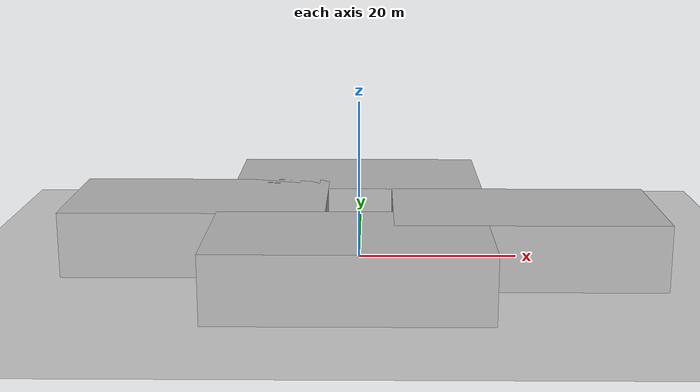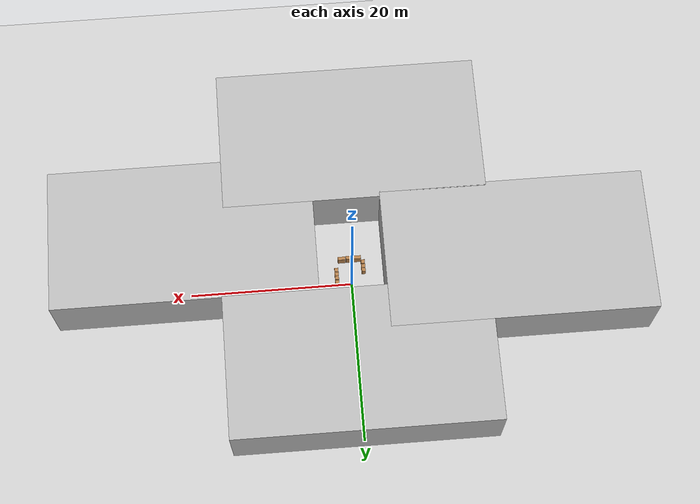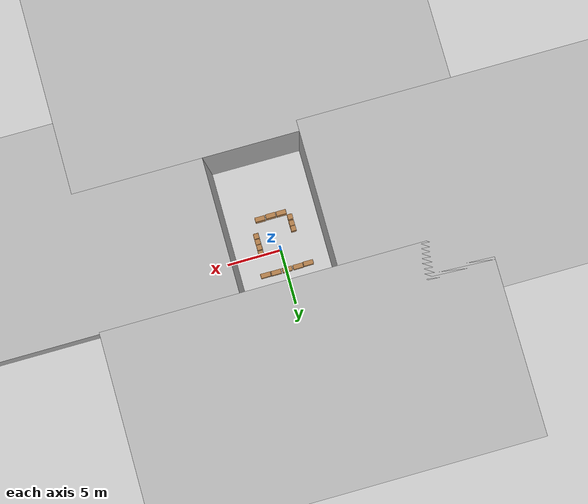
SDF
<sdf version='1.7'>
  <world name='default'>
  <plugin filename="gz-sim-physics-system" name="gz::sim::systems::Physics"></plugin>
  <plugin filename="gz-sim-user-commands-system" name="gz::sim::systems::UserCommands"></plugin>
  <plugin filename="gz-sim-scene-broadcaster-system" name="gz::sim::systems::SceneBroadcaster"></plugin>
  <plugin filename="gz-sim-sensors-system" name="gz::sim::systems::Sensors">
    <render_engine>ogre2</render_engine>
  </plugin>
    <light name='sun' type='directional'>
      <cast_shadows>1</cast_shadows>
      <pose>0 0 10 0 -0 0</pose>
      <diffuse>0.8 0.8 0.8 1</diffuse>
      <specular>0.2 0.2 0.2 1</specular>
      <attenuation>
        <range>1000</range>
        <constant>0.9</constant>
        <linear>0.01</linear>
        <quadratic>0.001</quadratic>
      </attenuation>
      <direction>-0.5 0.1 -0.9</direction>
      <spot>
        <inner_angle>0</inner_angle>
        <outer_angle>0</outer_angle>
        <falloff>0</falloff>
      </spot>
    </light>
    <model name='ground_plane'>
      <static>1</static>
      <link name='link'>
        <collision name='collision'>
          <geometry>
            <plane>
              <normal>0 0 1</normal>
              <size>100 100</size>
            </plane>
          </geometry>
          <surface>
            <contact>
              <collide_bitmask>65535</collide_bitmask>
              <ode/>
            </contact>
            <friction>
              <ode>
                <mu>100</mu>
                <mu2>50</mu2>
              </ode>
              <torsional>
                <ode/>
              </torsional>
            </friction>
            <bounce/>
          </surface>
          <max_contacts>10</max_contacts>
        </collision>
        <visual name='visual'>
          <cast_shadows>0</cast_shadows>
          <geometry>
            <plane>
              <normal>0 0 1</normal>
              <size>100 100</size>
            </plane>
          </geometry>
          <material>
            <script>
              <uri>file://media/materials/scripts/gazebo.material</uri>
              <name>Gazebo/Grey</name>
            </script>
          </material>
        </visual>
        <self_collide>0</self_collide>
        <enable_wind>0</enable_wind>
        <kinematic>0</kinematic>
      </link>
    </model>
    <gravity>0 0 -9.8</gravity>
    <magnetic_field>6e-06 2.3e-05 -4.2e-05</magnetic_field>
    <atmosphere type='adiabatic'/>
    <physics type='ode'>
      <max_step_size>0.001</max_step_size>
      <real_time_factor>1</real_time_factor>
      <real_time_update_rate>1000</real_time_update_rate>
    </physics>
    <scene>
      <ambient>0.4 0.4 0.4 1</ambient>
      <background>0.7 0.7 0.7 1</background>
      <shadows>1</shadows>
    </scene>
    <audio>
      <device>default</device>
    </audio>
    <wind/>
    <spherical_coordinates>
      <surface_model>EARTH_WGS84</surface_model>
      <latitude_deg>0</latitude_deg>
      <longitude_deg>0</longitude_deg>
      <elevation>0</elevation>
      <heading_deg>0</heading_deg>
    </spherical_coordinates>
    <model name='cabinet'>
      <static>1</static>
      <link name='cabinet_bottom_plate'>
        <inertial>
          <pose>0 0 -1 0 -0 0</pose>
          <inertia>
            <ixx>2.05</ixx>
            <ixy>0</ixy>
            <ixz>0</ixz>
            <iyy>2.05</iyy>
            <iyz>0</iyz>
            <izz>2.05</izz>
          </inertia>
          <mass>25</mass>
        </inertial>
        <collision name='cabinet_bottom_plate_geom'>
          <pose>0 0 0.01 0 -0 0</pose>
          <geometry>
            <box>
              <size>0.45 0.45 0.02</size>
            </box>
          </geometry>
          <max_contacts>10</max_contacts>
          <surface>
            <contact>
              <ode/>
            </contact>
            <bounce/>
            <friction>
              <torsional>
                <ode/>
              </torsional>
              <ode/>
            </friction>
          </surface>
        </collision>
        <visual name='cabinet_bottom_plate_geom_visual'>
          <pose>0 0 0.01 0 -0 0</pose>
          <geometry>
            <box>
              <size>0.45 0.45 0.02</size>
            </box>
          </geometry>
          <material>
            <script>
              <uri>file://media/materials/scripts/gazebo.material</uri>
              <name>Gazebo/Wood</name>
            </script>
          </material>
        </visual>
        <collision name='cabinet_bottom_plate_geom_cabinet_back_plate'>
          <pose>0.235 0 0.51 0 -0 0</pose>
          <geometry>
            <box>
              <size>0.02 0.45 1.02</size>
            </box>
          </geometry>
          <max_contacts>10</max_contacts>
          <surface>
            <contact>
              <ode/>
            </contact>
            <bounce/>
            <friction>
              <torsional>
                <ode/>
              </torsional>
              <ode/>
            </friction>
          </surface>
        </collision>
        <visual name='cabinet_bottom_plate_geom_cabinet_back_plate_visual'>
          <pose>0.235 0 0.51 0 -0 0</pose>
          <geometry>
            <box>
              <size>0.02 0.45 1.02</size>
            </box>
          </geometry>
          <material>
            <script>
              <uri>file://media/materials/scripts/gazebo.material</uri>
              <name>Gazebo/Wood</name>
            </script>
          </material>
        </visual>
        <collision name='cabinet_bottom_plate_geom_cabinet_left_plate'>
          <pose>0 0.235 0.51 0 -0 0</pose>
          <geometry>
            <box>
              <size>0.45 0.02 1.02</size>
            </box>
          </geometry>
          <max_contacts>10</max_contacts>
          <surface>
            <contact>
              <ode/>
            </contact>
            <bounce/>
            <friction>
              <torsional>
                <ode/>
              </torsional>
              <ode/>
            </friction>
          </surface>
        </collision>
        <visual name='cabinet_bottom_plate_geom_cabinet_left_plate_visual'>
          <pose>0 0.235 0.51 0 -0 0</pose>
          <geometry>
            <box>
              <size>0.45 0.02 1.02</size>
            </box>
          </geometry>
          <material>
            <script>
              <uri>file://media/materials/scripts/gazebo.material</uri>
              <name>Gazebo/Wood</name>
            </script>
          </material>
        </visual>
        <collision name='cabinet_bottom_plate_geom_cabinet_middle_plate'>
          <pose>0 0 0.51 0 -0 0</pose>
          <geometry>
            <box>
              <size>0.45 0.45 0.02</size>
            </box>
          </geometry>
          <max_contacts>10</max_contacts>
          <surface>
            <contact>
              <ode/>
            </contact>
            <bounce/>
            <friction>
              <torsional>
                <ode/>
              </torsional>
              <ode/>
            </friction>
          </surface>
        </collision>
        <visual name='cabinet_bottom_plate_geom_cabinet_middle_plate_visual'>
          <pose>0 0 0.51 0 -0 0</pose>
          <geometry>
            <box>
              <size>0.45 0.45 0.02</size>
            </box>
          </geometry>
          <material>
            <script>
              <uri>file://media/materials/scripts/gazebo.material</uri>
              <name>Gazebo/Wood</name>
            </script>
          </material>
        </visual>
        <collision name='cabinet_bottom_plate_geom_cabinet_right_plate'>
          <pose>0 -0.235 0.51 0 -0 0</pose>
          <geometry>
            <box>
              <size>0.45 0.02 1.02</size>
            </box>
          </geometry>
          <max_contacts>10</max_contacts>
          <surface>
            <contact>
              <ode/>
            </contact>
            <bounce/>
            <friction>
              <torsional>
                <ode/>
              </torsional>
              <ode/>
            </friction>
          </surface>
        </collision>
        <visual name='cabinet_bottom_plate_geom_cabinet_right_plate_visual'>
          <pose>0 -0.235 0.51 0 -0 0</pose>
          <geometry>
            <box>
              <size>0.45 0.02 1.02</size>
            </box>
          </geometry>
          <material>
            <script>
              <uri>file://media/materials/scripts/gazebo.material</uri>
              <name>Gazebo/Wood</name>
            </script>
          </material>
        </visual>
        <collision name='cabinet_bottom_plate_geom_cabinet_top_plate'>
          <pose>0 0 1.01 0 -0 0</pose>
          <geometry>
            <box>
              <size>0.45 0.45 0.02</size>
            </box>
          </geometry>
          <max_contacts>10</max_contacts>
          <surface>
            <contact>
              <ode/>
            </contact>
            <bounce/>
            <friction>
              <torsional>
                <ode/>
              </torsional>
              <ode/>
            </friction>
          </surface>
        </collision>
        <visual name='cabinet_bottom_plate_geom_cabinet_top_plate_visual'>
          <pose>0 0 1.01 0 -0 0</pose>
          <geometry>
            <box>
              <size>0.45 0.45 0.02</size>
            </box>
          </geometry>
          <material>
            <script>
              <uri>file://media/materials/scripts/gazebo.material</uri>
              <name>Gazebo/Wood</name>
            </script>
          </material>
        </visual>
        <self_collide>0</self_collide>
        <enable_wind>0</enable_wind>
        <kinematic>0</kinematic>
      </link>
      <pose>1.79653 -1.74057 0 0 -0 0</pose>
    </model>
    <model name='cabinet_0'>
      <static>1</static>
      <link name='cabinet_bottom_plate'>
        <inertial>
          <pose>0 0 -1 0 -0 0</pose>
          <inertia>
            <ixx>2.05</ixx>
            <ixy>0</ixy>
            <ixz>0</ixz>
            <iyy>2.05</iyy>
            <iyz>0</iyz>
            <izz>2.05</izz>
          </inertia>
          <mass>25</mass>
        </inertial>
        <collision name='cabinet_bottom_plate_geom'>
          <pose>0 0 0.01 0 -0 0</pose>
          <geometry>
            <box>
              <size>0.45 0.45 0.02</size>
            </box>
          </geometry>
          <max_contacts>10</max_contacts>
          <surface>
            <contact>
              <ode/>
            </contact>
            <bounce/>
            <friction>
              <torsional>
                <ode/>
              </torsional>
              <ode/>
            </friction>
          </surface>
        </collision>
        <visual name='cabinet_bottom_plate_geom_visual'>
          <pose>0 0 0.01 0 -0 0</pose>
          <geometry>
            <box>
              <size>0.45 0.45 0.02</size>
            </box>
          </geometry>
          <material>
            <script>
              <uri>file://media/materials/scripts/gazebo.material</uri>
              <name>Gazebo/Wood</name>
            </script>
          </material>
        </visual>
        <collision name='cabinet_bottom_plate_geom_cabinet_back_plate'>
          <pose>0.235 0 0.51 0 -0 0</pose>
          <geometry>
            <box>
              <size>0.02 0.45 1.02</size>
            </box>
          </geometry>
          <max_contacts>10</max_contacts>
          <surface>
            <contact>
              <ode/>
            </contact>
            <bounce/>
            <friction>
              <torsional>
                <ode/>
              </torsional>
              <ode/>
            </friction>
          </surface>
        </collision>
        <visual name='cabinet_bottom_plate_geom_cabinet_back_plate_visual'>
          <pose>0.235 0 0.51 0 -0 0</pose>
          <geometry>
            <box>
              <size>0.02 0.45 1.02</size>
            </box>
          </geometry>
          <material>
            <script>
              <uri>file://media/materials/scripts/gazebo.material</uri>
              <name>Gazebo/Wood</name>
            </script>
          </material>
        </visual>
        <collision name='cabinet_bottom_plate_geom_cabinet_left_plate'>
          <pose>0 0.235 0.51 0 -0 0</pose>
          <geometry>
            <box>
              <size>0.45 0.02 1.02</size>
            </box>
          </geometry>
          <max_contacts>10</max_contacts>
          <surface>
            <contact>
              <ode/>
            </contact>
            <bounce/>
            <friction>
              <torsional>
                <ode/>
              </torsional>
              <ode/>
            </friction>
          </surface>
        </collision>
        <visual name='cabinet_bottom_plate_geom_cabinet_left_plate_visual'>
          <pose>0 0.235 0.51 0 -0 0</pose>
          <geometry>
            <box>
              <size>0.45 0.02 1.02</size>
            </box>
          </geometry>
          <material>
            <script>
              <uri>file://media/materials/scripts/gazebo.material</uri>
              <name>Gazebo/Wood</name>
            </script>
          </material>
        </visual>
        <collision name='cabinet_bottom_plate_geom_cabinet_middle_plate'>
          <pose>0 0 0.51 0 -0 0</pose>
          <geometry>
            <box>
              <size>0.45 0.45 0.02</size>
            </box>
          </geometry>
          <max_contacts>10</max_contacts>
          <surface>
            <contact>
              <ode/>
            </contact>
            <bounce/>
            <friction>
              <torsional>
                <ode/>
              </torsional>
              <ode/>
            </friction>
          </surface>
        </collision>
        <visual name='cabinet_bottom_plate_geom_cabinet_middle_plate_visual'>
          <pose>0 0 0.51 0 -0 0</pose>
          <geometry>
            <box>
              <size>0.45 0.45 0.02</size>
            </box>
          </geometry>
          <material>
            <script>
              <uri>file://media/materials/scripts/gazebo.material</uri>
              <name>Gazebo/Wood</name>
            </script>
          </material>
        </visual>
        <collision name='cabinet_bottom_plate_geom_cabinet_right_plate'>
          <pose>0 -0.235 0.51 0 -0 0</pose>
          <geometry>
            <box>
              <size>0.45 0.02 1.02</size>
            </box>
          </geometry>
          <max_contacts>10</max_contacts>
          <surface>
            <contact>
              <ode/>
            </contact>
            <bounce/>
            <friction>
              <torsional>
                <ode/>
              </torsional>
              <ode/>
            </friction>
          </surface>
        </collision>
        <visual name='cabinet_bottom_plate_geom_cabinet_right_plate_visual'>
          <pose>0 -0.235 0.51 0 -0 0</pose>
          <geometry>
            <box>
              <size>0.45 0.02 1.02</size>
            </box>
          </geometry>
          <material>
            <script>
              <uri>file://media/materials/scripts/gazebo.material</uri>
              <name>Gazebo/Wood</name>
            </script>
          </material>
        </visual>
        <collision name='cabinet_bottom_plate_geom_cabinet_top_plate'>
          <pose>0 0 1.01 0 -0 0</pose>
          <geometry>
            <box>
              <size>0.45 0.45 0.02</size>
            </box>
          </geometry>
          <max_contacts>10</max_contacts>
          <surface>
            <contact>
              <ode/>
            </contact>
            <bounce/>
            <friction>
              <torsional>
                <ode/>
              </torsional>
              <ode/>
            </friction>
          </surface>
        </collision>
        <visual name='cabinet_bottom_plate_geom_cabinet_top_plate_visual'>
          <pose>0 0 1.01 0 -0 0</pose>
          <geometry>
            <box>
              <size>0.45 0.45 0.02</size>
            </box>
          </geometry>
          <material>
            <script>
              <uri>file://media/materials/scripts/gazebo.material</uri>
              <name>Gazebo/Wood</name>
            </script>
          </material>
        </visual>
        <self_collide>0</self_collide>
        <enable_wind>0</enable_wind>
        <kinematic>0</kinematic>
      </link>
      <pose>-1.58608 -1.53469 0 0 -0 0</pose>
    </model>
    <model name='bookshelf'>
      <static>1</static>
      <link name='link'>
        <inertial>
          <mass>1</mass>
        </inertial>
        <collision name='back'>
          <pose>0 0.005 0.6 0 -0 0</pose>
          <geometry>
            <box>
              <size>0.9 0.01 1.2</size>
            </box>
          </geometry>
          <max_contacts>10</max_contacts>
          <surface>
            <contact>
              <ode/>
            </contact>
            <bounce/>
            <friction>
              <torsional>
                <ode/>
              </torsional>
              <ode/>
            </friction>
          </surface>
        </collision>
        <visual name='visual1'>
          <pose>0 0.005 0.6 0 -0 0</pose>
          <geometry>
            <box>
              <size>0.9 0.01 1.2</size>
            </box>
          </geometry>
          <material>
            <script>
              <uri>file://media/materials/scripts/gazebo.material</uri>
              <name>Gazebo/Wood</name>
            </script>
          </material>
        </visual>
        <collision name='left_side'>
          <pose>0.45 -0.195 0.6 0 -0 0</pose>
          <geometry>
            <box>
              <size>0.02 0.4 1.2</size>
            </box>
          </geometry>
          <max_contacts>10</max_contacts>
          <surface>
            <contact>
              <ode/>
            </contact>
            <bounce/>
            <friction>
              <torsional>
                <ode/>
              </torsional>
              <ode/>
            </friction>
          </surface>
        </collision>
        <visual name='visual2'>
          <pose>0.45 -0.195 0.6 0 -0 0</pose>
          <geometry>
            <box>
              <size>0.02 0.4 1.2</size>
            </box>
          </geometry>
          <material>
            <script>
              <uri>file://media/materials/scripts/gazebo.material</uri>
              <name>Gazebo/Wood</name>
            </script>
          </material>
        </visual>
        <collision name='right_side'>
          <pose>-0.45 -0.195 0.6 0 -0 0</pose>
          <geometry>
            <box>
              <size>0.02 0.4 1.2</size>
            </box>
          </geometry>
          <max_contacts>10</max_contacts>
          <surface>
            <contact>
              <ode/>
            </contact>
            <bounce/>
            <friction>
              <torsional>
                <ode/>
              </torsional>
              <ode/>
            </friction>
          </surface>
        </collision>
        <visual name='visual3'>
          <pose>-0.45 -0.195 0.6 0 -0 0</pose>
          <geometry>
            <box>
              <size>0.02 0.4 1.2</size>
            </box>
          </geometry>
          <material>
            <script>
              <uri>file://media/materials/scripts/gazebo.material</uri>
              <name>Gazebo/Wood</name>
            </script>
          </material>
        </visual>
        <collision name='bottom'>
          <pose>0 -0.195 0.03 0 -0 0</pose>
          <geometry>
            <box>
              <size>0.88 0.4 0.06</size>
            </box>
          </geometry>
          <max_contacts>10</max_contacts>
          <surface>
            <contact>
              <ode/>
            </contact>
            <bounce/>
            <friction>
              <torsional>
                <ode/>
              </torsional>
              <ode/>
            </friction>
          </surface>
        </collision>
        <visual name='visual4'>
          <pose>0 -0.195 0.03 0 -0 0</pose>
          <geometry>
            <box>
              <size>0.88 0.4 0.06</size>
            </box>
          </geometry>
          <material>
            <script>
              <uri>file://media/materials/scripts/gazebo.material</uri>
              <name>Gazebo/Wood</name>
            </script>
          </material>
        </visual>
        <collision name='top'>
          <pose>0 -0.195 1.19 0 -0 0</pose>
          <geometry>
            <box>
              <size>0.88 0.4 0.02</size>
            </box>
          </geometry>
          <max_contacts>10</max_contacts>
          <surface>
            <contact>
              <ode/>
            </contact>
            <bounce/>
            <friction>
              <torsional>
                <ode/>
              </torsional>
              <ode/>
            </friction>
          </surface>
        </collision>
        <visual name='visual5'>
          <pose>0 -0.195 1.19 0 -0 0</pose>
          <geometry>
            <box>
              <size>0.88 0.4 0.02</size>
            </box>
          </geometry>
          <material>
            <script>
              <uri>file://media/materials/scripts/gazebo.material</uri>
              <name>Gazebo/Wood</name>
            </script>
          </material>
        </visual>
        <collision name='low_shelf'>
          <pose>0 -0.195 0.43 0 -0 0</pose>
          <geometry>
            <box>
              <size>0.88 0.4 0.02</size>
            </box>
          </geometry>
          <max_contacts>10</max_contacts>
          <surface>
            <contact>
              <ode/>
            </contact>
            <bounce/>
            <friction>
              <torsional>
                <ode/>
              </torsional>
              <ode/>
            </friction>
          </surface>
        </collision>
        <visual name='visual6'>
          <pose>0 -0.195 0.43 0 -0 0</pose>
          <geometry>
            <box>
              <size>0.88 0.4 0.02</size>
            </box>
          </geometry>
          <material>
            <script>
              <uri>file://media/materials/scripts/gazebo.material</uri>
              <name>Gazebo/Wood</name>
            </script>
          </material>
        </visual>
        <collision name='high_shelf'>
          <pose>0 -0.195 0.8 0 -0 0</pose>
          <geometry>
            <box>
              <size>0.88 0.4 0.02</size>
            </box>
          </geometry>
          <max_contacts>10</max_contacts>
          <surface>
            <contact>
              <ode/>
            </contact>
            <bounce/>
            <friction>
              <torsional>
                <ode/>
              </torsional>
              <ode/>
            </friction>
          </surface>
        </collision>
        <visual name='visual7'>
          <pose>0 -0.195 0.8 0 -0 0</pose>
          <geometry>
            <box>
              <size>0.88 0.4 0.02</size>
            </box>
          </geometry>
          <material>
            <script>
              <uri>file://media/materials/scripts/gazebo.material</uri>
              <name>Gazebo/Wood</name>
            </script>
          </material>
        </visual>
        <self_collide>0</self_collide>
        <enable_wind>0</enable_wind>
        <kinematic>0</kinematic>
      </link>
      <pose>-0.070143 2.05105 0 0 -0 0</pose>
    </model>
    <model name='bookshelf_0'>
      <static>1</static>
      <link name='link'>
        <inertial>
          <mass>1</mass>
        </inertial>
        <collision name='back'>
          <pose>0 0.005 0.6 0 -0 0</pose>
          <geometry>
            <box>
              <size>0.9 0.01 1.2</size>
            </box>
          </geometry>
          <max_contacts>10</max_contacts>
          <surface>
            <contact>
              <ode/>
            </contact>
            <bounce/>
            <friction>
              <torsional>
                <ode/>
              </torsional>
              <ode/>
            </friction>
          </surface>
        </collision>
        <visual name='visual1'>
          <pose>0 0.005 0.6 0 -0 0</pose>
          <geometry>
            <box>
              <size>0.9 0.01 1.2</size>
            </box>
          </geometry>
          <material>
            <script>
              <uri>file://media/materials/scripts/gazebo.material</uri>
              <name>Gazebo/Wood</name>
            </script>
          </material>
        </visual>
        <collision name='left_side'>
          <pose>0.45 -0.195 0.6 0 -0 0</pose>
          <geometry>
            <box>
              <size>0.02 0.4 1.2</size>
            </box>
          </geometry>
          <max_contacts>10</max_contacts>
          <surface>
            <contact>
              <ode/>
            </contact>
            <bounce/>
            <friction>
              <torsional>
                <ode/>
              </torsional>
              <ode/>
            </friction>
          </surface>
        </collision>
        <visual name='visual2'>
          <pose>0.45 -0.195 0.6 0 -0 0</pose>
          <geometry>
            <box>
              <size>0.02 0.4 1.2</size>
            </box>
          </geometry>
          <material>
            <script>
              <uri>file://media/materials/scripts/gazebo.material</uri>
              <name>Gazebo/Wood</name>
            </script>
          </material>
        </visual>
        <collision name='right_side'>
          <pose>-0.45 -0.195 0.6 0 -0 0</pose>
          <geometry>
            <box>
              <size>0.02 0.4 1.2</size>
            </box>
          </geometry>
          <max_contacts>10</max_contacts>
          <surface>
            <contact>
              <ode/>
            </contact>
            <bounce/>
            <friction>
              <torsional>
                <ode/>
              </torsional>
              <ode/>
            </friction>
          </surface>
        </collision>
        <visual name='visual3'>
          <pose>-0.45 -0.195 0.6 0 -0 0</pose>
          <geometry>
            <box>
              <size>0.02 0.4 1.2</size>
            </box>
          </geometry>
          <material>
            <script>
              <uri>file://media/materials/scripts/gazebo.material</uri>
              <name>Gazebo/Wood</name>
            </script>
          </material>
        </visual>
        <collision name='bottom'>
          <pose>0 -0.195 0.03 0 -0 0</pose>
          <geometry>
            <box>
              <size>0.88 0.4 0.06</size>
            </box>
          </geometry>
          <max_contacts>10</max_contacts>
          <surface>
            <contact>
              <ode/>
            </contact>
            <bounce/>
            <friction>
              <torsional>
                <ode/>
              </torsional>
              <ode/>
            </friction>
          </surface>
        </collision>
        <visual name='visual4'>
          <pose>0 -0.195 0.03 0 -0 0</pose>
          <geometry>
            <box>
              <size>0.88 0.4 0.06</size>
            </box>
          </geometry>
          <material>
            <script>
              <uri>file://media/materials/scripts/gazebo.material</uri>
              <name>Gazebo/Wood</name>
            </script>
          </material>
        </visual>
        <collision name='top'>
          <pose>0 -0.195 1.19 0 -0 0</pose>
          <geometry>
            <box>
              <size>0.88 0.4 0.02</size>
            </box>
          </geometry>
          <max_contacts>10</max_contacts>
          <surface>
            <contact>
              <ode/>
            </contact>
            <bounce/>
            <friction>
              <torsional>
                <ode/>
              </torsional>
              <ode/>
            </friction>
          </surface>
        </collision>
        <visual name='visual5'>
          <pose>0 -0.195 1.19 0 -0 0</pose>
          <geometry>
            <box>
              <size>0.88 0.4 0.02</size>
            </box>
          </geometry>
          <material>
            <script>
              <uri>file://media/materials/scripts/gazebo.material</uri>
              <name>Gazebo/Wood</name>
            </script>
          </material>
        </visual>
        <collision name='low_shelf'>
          <pose>0 -0.195 0.43 0 -0 0</pose>
          <geometry>
            <box>
              <size>0.88 0.4 0.02</size>
            </box>
          </geometry>
          <max_contacts>10</max_contacts>
          <surface>
            <contact>
              <ode/>
            </contact>
            <bounce/>
            <friction>
              <torsional>
                <ode/>
              </torsional>
              <ode/>
            </friction>
          </surface>
        </collision>
        <visual name='visual6'>
          <pose>0 -0.195 0.43 0 -0 0</pose>
          <geometry>
            <box>
              <size>0.88 0.4 0.02</size>
            </box>
          </geometry>
          <material>
            <script>
              <uri>file://media/materials/scripts/gazebo.material</uri>
              <name>Gazebo/Wood</name>
            </script>
          </material>
        </visual>
        <collision name='high_shelf'>
          <pose>0 -0.195 0.8 0 -0 0</pose>
          <geometry>
            <box>
              <size>0.88 0.4 0.02</size>
            </box>
          </geometry>
          <max_contacts>10</max_contacts>
          <surface>
            <contact>
              <ode/>
            </contact>
            <bounce/>
            <friction>
              <torsional>
                <ode/>
              </torsional>
              <ode/>
            </friction>
          </surface>
        </collision>
        <visual name='visual7'>
          <pose>0 -0.195 0.8 0 -0 0</pose>
          <geometry>
            <box>
              <size>0.88 0.4 0.02</size>
            </box>
          </geometry>
          <material>
            <script>
              <uri>file://media/materials/scripts/gazebo.material</uri>
              <name>Gazebo/Wood</name>
            </script>
          </material>
        </visual>
        <self_collide>0</self_collide>
        <enable_wind>0</enable_wind>
        <kinematic>0</kinematic>
      </link>
      <pose>0.942437 2.04598 0 0 -0 0</pose>
    </model>
    <model name='bookshelf_1'>
      <static>1</static>
      <link name='link'>
        <inertial>
          <mass>1</mass>
        </inertial>
        <collision name='back'>
          <pose>0 0.005 0.6 0 -0 0</pose>
          <geometry>
            <box>
              <size>0.9 0.01 1.2</size>
            </box>
          </geometry>
          <max_contacts>10</max_contacts>
          <surface>
            <contact>
              <ode/>
            </contact>
            <bounce/>
            <friction>
              <torsional>
                <ode/>
              </torsional>
              <ode/>
            </friction>
          </surface>
        </collision>
        <visual name='visual1'>
          <pose>0 0.005 0.6 0 -0 0</pose>
          <geometry>
            <box>
              <size>0.9 0.01 1.2</size>
            </box>
          </geometry>
          <material>
            <script>
              <uri>file://media/materials/scripts/gazebo.material</uri>
              <name>Gazebo/Wood</name>
            </script>
          </material>
        </visual>
        <collision name='left_side'>
          <pose>0.45 -0.195 0.6 0 -0 0</pose>
          <geometry>
            <box>
              <size>0.02 0.4 1.2</size>
            </box>
          </geometry>
          <max_contacts>10</max_contacts>
          <surface>
            <contact>
              <ode/>
            </contact>
            <bounce/>
            <friction>
              <torsional>
                <ode/>
              </torsional>
              <ode/>
            </friction>
          </surface>
        </collision>
        <visual name='visual2'>
          <pose>0.45 -0.195 0.6 0 -0 0</pose>
          <geometry>
            <box>
              <size>0.02 0.4 1.2</size>
            </box>
          </geometry>
          <material>
            <script>
              <uri>file://media/materials/scripts/gazebo.material</uri>
              <name>Gazebo/Wood</name>
            </script>
          </material>
        </visual>
        <collision name='right_side'>
          <pose>-0.45 -0.195 0.6 0 -0 0</pose>
          <geometry>
            <box>
              <size>0.02 0.4 1.2</size>
            </box>
          </geometry>
          <max_contacts>10</max_contacts>
          <surface>
            <contact>
              <ode/>
            </contact>
            <bounce/>
            <friction>
              <torsional>
                <ode/>
              </torsional>
              <ode/>
            </friction>
          </surface>
        </collision>
        <visual name='visual3'>
          <pose>-0.45 -0.195 0.6 0 -0 0</pose>
          <geometry>
            <box>
              <size>0.02 0.4 1.2</size>
            </box>
          </geometry>
          <material>
            <script>
              <uri>file://media/materials/scripts/gazebo.material</uri>
              <name>Gazebo/Wood</name>
            </script>
          </material>
        </visual>
        <collision name='bottom'>
          <pose>0 -0.195 0.03 0 -0 0</pose>
          <geometry>
            <box>
              <size>0.88 0.4 0.06</size>
            </box>
          </geometry>
          <max_contacts>10</max_contacts>
          <surface>
            <contact>
              <ode/>
            </contact>
            <bounce/>
            <friction>
              <torsional>
                <ode/>
              </torsional>
              <ode/>
            </friction>
          </surface>
        </collision>
        <visual name='visual4'>
          <pose>0 -0.195 0.03 0 -0 0</pose>
          <geometry>
            <box>
              <size>0.88 0.4 0.06</size>
            </box>
          </geometry>
          <material>
            <script>
              <uri>file://media/materials/scripts/gazebo.material</uri>
              <name>Gazebo/Wood</name>
            </script>
          </material>
        </visual>
        <collision name='top'>
          <pose>0 -0.195 1.19 0 -0 0</pose>
          <geometry>
            <box>
              <size>0.88 0.4 0.02</size>
            </box>
          </geometry>
          <max_contacts>10</max_contacts>
          <surface>
            <contact>
              <ode/>
            </contact>
            <bounce/>
            <friction>
              <torsional>
                <ode/>
              </torsional>
              <ode/>
            </friction>
          </surface>
        </collision>
        <visual name='visual5'>
          <pose>0 -0.195 1.19 0 -0 0</pose>
          <geometry>
            <box>
              <size>0.88 0.4 0.02</size>
            </box>
          </geometry>
          <material>
            <script>
              <uri>file://media/materials/scripts/gazebo.material</uri>
              <name>Gazebo/Wood</name>
            </script>
          </material>
        </visual>
        <collision name='low_shelf'>
          <pose>0 -0.195 0.43 0 -0 0</pose>
          <geometry>
            <box>
              <size>0.88 0.4 0.02</size>
            </box>
          </geometry>
          <max_contacts>10</max_contacts>
          <surface>
            <contact>
              <ode/>
            </contact>
            <bounce/>
            <friction>
              <torsional>
                <ode/>
              </torsional>
              <ode/>
            </friction>
          </surface>
        </collision>
        <visual name='visual6'>
          <pose>0 -0.195 0.43 0 -0 0</pose>
          <geometry>
            <box>
              <size>0.88 0.4 0.02</size>
            </box>
          </geometry>
          <material>
            <script>
              <uri>file://media/materials/scripts/gazebo.material</uri>
              <name>Gazebo/Wood</name>
            </script>
          </material>
        </visual>
        <collision name='high_shelf'>
          <pose>0 -0.195 0.8 0 -0 0</pose>
          <geometry>
            <box>
              <size>0.88 0.4 0.02</size>
            </box>
          </geometry>
          <max_contacts>10</max_contacts>
          <surface>
            <contact>
              <ode/>
            </contact>
            <bounce/>
            <friction>
              <torsional>
                <ode/>
              </torsional>
              <ode/>
            </friction>
          </surface>
        </collision>
        <visual name='visual7'>
          <pose>0 -0.195 0.8 0 -0 0</pose>
          <geometry>
            <box>
              <size>0.88 0.4 0.02</size>
            </box>
          </geometry>
          <material>
            <script>
              <uri>file://media/materials/scripts/gazebo.material</uri>
              <name>Gazebo/Wood</name>
            </script>
          </material>
        </visual>
        <self_collide>0</self_collide>
        <enable_wind>0</enable_wind>
        <kinematic>0</kinematic>
      </link>
      <pose>-1.06941 2.03933 0 0 -0 0</pose>
    </model>
    <model name='bookshelf_2'>
      <static>1</static>
      <link name='link'>
        <inertial>
          <mass>1</mass>
        </inertial>
        <collision name='back'>
          <pose>0 0.005 0.6 0 -0 0</pose>
          <geometry>
            <box>
              <size>0.9 0.01 1.2</size>
            </box>
          </geometry>
          <max_contacts>10</max_contacts>
          <surface>
            <contact>
              <ode/>
            </contact>
            <bounce/>
            <friction>
              <torsional>
                <ode/>
              </torsional>
              <ode/>
            </friction>
          </surface>
        </collision>
        <visual name='visual1'>
          <pose>0 0.005 0.6 0 -0 0</pose>
          <geometry>
            <box>
              <size>0.9 0.01 1.2</size>
            </box>
          </geometry>
          <material>
            <script>
              <uri>file://media/materials/scripts/gazebo.material</uri>
              <name>Gazebo/Wood</name>
            </script>
          </material>
        </visual>
        <collision name='left_side'>
          <pose>0.45 -0.195 0.6 0 -0 0</pose>
          <geometry>
            <box>
              <size>0.02 0.4 1.2</size>
            </box>
          </geometry>
          <max_contacts>10</max_contacts>
          <surface>
            <contact>
              <ode/>
            </contact>
            <bounce/>
            <friction>
              <torsional>
                <ode/>
              </torsional>
              <ode/>
            </friction>
          </surface>
        </collision>
        <visual name='visual2'>
          <pose>0.45 -0.195 0.6 0 -0 0</pose>
          <geometry>
            <box>
              <size>0.02 0.4 1.2</size>
            </box>
          </geometry>
          <material>
            <script>
              <uri>file://media/materials/scripts/gazebo.material</uri>
              <name>Gazebo/Wood</name>
            </script>
          </material>
        </visual>
        <collision name='right_side'>
          <pose>-0.45 -0.195 0.6 0 -0 0</pose>
          <geometry>
            <box>
              <size>0.02 0.4 1.2</size>
            </box>
          </geometry>
          <max_contacts>10</max_contacts>
          <surface>
            <contact>
              <ode/>
            </contact>
            <bounce/>
            <friction>
              <torsional>
                <ode/>
              </torsional>
              <ode/>
            </friction>
          </surface>
        </collision>
        <visual name='visual3'>
          <pose>-0.45 -0.195 0.6 0 -0 0</pose>
          <geometry>
            <box>
              <size>0.02 0.4 1.2</size>
            </box>
          </geometry>
          <material>
            <script>
              <uri>file://media/materials/scripts/gazebo.material</uri>
              <name>Gazebo/Wood</name>
            </script>
          </material>
        </visual>
        <collision name='bottom'>
          <pose>0 -0.195 0.03 0 -0 0</pose>
          <geometry>
            <box>
              <size>0.88 0.4 0.06</size>
            </box>
          </geometry>
          <max_contacts>10</max_contacts>
          <surface>
            <contact>
              <ode/>
            </contact>
            <bounce/>
            <friction>
              <torsional>
                <ode/>
              </torsional>
              <ode/>
            </friction>
          </surface>
        </collision>
        <visual name='visual4'>
          <pose>0 -0.195 0.03 0 -0 0</pose>
          <geometry>
            <box>
              <size>0.88 0.4 0.06</size>
            </box>
          </geometry>
          <material>
            <script>
              <uri>file://media/materials/scripts/gazebo.material</uri>
              <name>Gazebo/Wood</name>
            </script>
          </material>
        </visual>
        <collision name='top'>
          <pose>0 -0.195 1.19 0 -0 0</pose>
          <geometry>
            <box>
              <size>0.88 0.4 0.02</size>
            </box>
          </geometry>
          <max_contacts>10</max_contacts>
          <surface>
            <contact>
              <ode/>
            </contact>
            <bounce/>
            <friction>
              <torsional>
                <ode/>
              </torsional>
              <ode/>
            </friction>
          </surface>
        </collision>
        <visual name='visual5'>
          <pose>0 -0.195 1.19 0 -0 0</pose>
          <geometry>
            <box>
              <size>0.88 0.4 0.02</size>
            </box>
          </geometry>
          <material>
            <script>
              <uri>file://media/materials/scripts/gazebo.material</uri>
              <name>Gazebo/Wood</name>
            </script>
          </material>
        </visual>
        <collision name='low_shelf'>
          <pose>0 -0.195 0.43 0 -0 0</pose>
          <geometry>
            <box>
              <size>0.88 0.4 0.02</size>
            </box>
          </geometry>
          <max_contacts>10</max_contacts>
          <surface>
            <contact>
              <ode/>
            </contact>
            <bounce/>
            <friction>
              <torsional>
                <ode/>
              </torsional>
              <ode/>
            </friction>
          </surface>
        </collision>
        <visual name='visual6'>
          <pose>0 -0.195 0.43 0 -0 0</pose>
          <geometry>
            <box>
              <size>0.88 0.4 0.02</size>
            </box>
          </geometry>
          <material>
            <script>
              <uri>file://media/materials/scripts/gazebo.material</uri>
              <name>Gazebo/Wood</name>
            </script>
          </material>
        </visual>
        <collision name='high_shelf'>
          <pose>0 -0.195 0.8 0 -0 0</pose>
          <geometry>
            <box>
              <size>0.88 0.4 0.02</size>
            </box>
          </geometry>
          <max_contacts>10</max_contacts>
          <surface>
            <contact>
              <ode/>
            </contact>
            <bounce/>
            <friction>
              <torsional>
                <ode/>
              </torsional>
              <ode/>
            </friction>
          </surface>
        </collision>
        <visual name='visual7'>
          <pose>0 -0.195 0.8 0 -0 0</pose>
          <geometry>
            <box>
              <size>0.88 0.4 0.02</size>
            </box>
          </geometry>
          <material>
            <script>
              <uri>file://media/materials/scripts/gazebo.material</uri>
              <name>Gazebo/Wood</name>
            </script>
          </material>
        </visual>
        <self_collide>0</self_collide>
        <enable_wind>0</enable_wind>
        <kinematic>0</kinematic>
      </link>
      <pose>-2.02264 2.00355 0 0 -0 0</pose>
    </model>
    <model name='cabinet_1'>
      <static>1</static>
      <link name='cabinet_bottom_plate'>
        <inertial>
          <pose>0 0 -1 0 -0 0</pose>
          <inertia>
            <ixx>2.05</ixx>
            <ixy>0</ixy>
            <ixz>0</ixz>
            <iyy>2.05</iyy>
            <iyz>0</iyz>
            <izz>2.05</izz>
          </inertia>
          <mass>25</mass>
        </inertial>
        <collision name='cabinet_bottom_plate_geom'>
          <pose>0 0 0.01 0 -0 0</pose>
          <geometry>
            <box>
              <size>0.45 0.45 0.02</size>
            </box>
          </geometry>
          <max_contacts>10</max_contacts>
          <surface>
            <contact>
              <ode/>
            </contact>
            <bounce/>
            <friction>
              <torsional>
                <ode/>
              </torsional>
              <ode/>
            </friction>
          </surface>
        </collision>
        <visual name='cabinet_bottom_plate_geom_visual'>
          <pose>0 0 0.01 0 -0 0</pose>
          <geometry>
            <box>
              <size>0.45 0.45 0.02</size>
            </box>
          </geometry>
          <material>
            <script>
              <uri>file://media/materials/scripts/gazebo.material</uri>
              <name>Gazebo/Wood</name>
            </script>
          </material>
        </visual>
        <collision name='cabinet_bottom_plate_geom_cabinet_back_plate'>
          <pose>0.235 0 0.51 0 -0 0</pose>
          <geometry>
            <box>
              <size>0.02 0.45 1.02</size>
            </box>
          </geometry>
          <max_contacts>10</max_contacts>
          <surface>
            <contact>
              <ode/>
            </contact>
            <bounce/>
            <friction>
              <torsional>
                <ode/>
              </torsional>
              <ode/>
            </friction>
          </surface>
        </collision>
        <visual name='cabinet_bottom_plate_geom_cabinet_back_plate_visual'>
          <pose>0.235 0 0.51 0 -0 0</pose>
          <geometry>
            <box>
              <size>0.02 0.45 1.02</size>
            </box>
          </geometry>
          <material>
            <script>
              <uri>file://media/materials/scripts/gazebo.material</uri>
              <name>Gazebo/Wood</name>
            </script>
          </material>
        </visual>
        <collision name='cabinet_bottom_plate_geom_cabinet_left_plate'>
          <pose>0 0.235 0.51 0 -0 0</pose>
          <geometry>
            <box>
              <size>0.45 0.02 1.02</size>
            </box>
          </geometry>
          <max_contacts>10</max_contacts>
          <surface>
            <contact>
              <ode/>
            </contact>
            <bounce/>
            <friction>
              <torsional>
                <ode/>
              </torsional>
              <ode/>
            </friction>
          </surface>
        </collision>
        <visual name='cabinet_bottom_plate_geom_cabinet_left_plate_visual'>
          <pose>0 0.235 0.51 0 -0 0</pose>
          <geometry>
            <box>
              <size>0.45 0.02 1.02</size>
            </box>
          </geometry>
          <material>
            <script>
              <uri>file://media/materials/scripts/gazebo.material</uri>
              <name>Gazebo/Wood</name>
            </script>
          </material>
        </visual>
        <collision name='cabinet_bottom_plate_geom_cabinet_middle_plate'>
          <pose>0 0 0.51 0 -0 0</pose>
          <geometry>
            <box>
              <size>0.45 0.45 0.02</size>
            </box>
          </geometry>
          <max_contacts>10</max_contacts>
          <surface>
            <contact>
              <ode/>
            </contact>
            <bounce/>
            <friction>
              <torsional>
                <ode/>
              </torsional>
              <ode/>
            </friction>
          </surface>
        </collision>
        <visual name='cabinet_bottom_plate_geom_cabinet_middle_plate_visual'>
          <pose>0 0 0.51 0 -0 0</pose>
          <geometry>
            <box>
              <size>0.45 0.45 0.02</size>
            </box>
          </geometry>
          <material>
            <script>
              <uri>file://media/materials/scripts/gazebo.material</uri>
              <name>Gazebo/Wood</name>
            </script>
          </material>
        </visual>
        <collision name='cabinet_bottom_plate_geom_cabinet_right_plate'>
          <pose>0 -0.235 0.51 0 -0 0</pose>
          <geometry>
            <box>
              <size>0.45 0.02 1.02</size>
            </box>
          </geometry>
          <max_contacts>10</max_contacts>
          <surface>
            <contact>
              <ode/>
            </contact>
            <bounce/>
            <friction>
              <torsional>
                <ode/>
              </torsional>
              <ode/>
            </friction>
          </surface>
        </collision>
        <visual name='cabinet_bottom_plate_geom_cabinet_right_plate_visual'>
          <pose>0 -0.235 0.51 0 -0 0</pose>
          <geometry>
            <box>
              <size>0.45 0.02 1.02</size>
            </box>
          </geometry>
          <material>
            <script>
              <uri>file://media/materials/scripts/gazebo.material</uri>
              <name>Gazebo/Wood</name>
            </script>
          </material>
        </visual>
        <collision name='cabinet_bottom_plate_geom_cabinet_top_plate'>
          <pose>0 0 1.01 0 -0 0</pose>
          <geometry>
            <box>
              <size>0.45 0.45 0.02</size>
            </box>
          </geometry>
          <max_contacts>10</max_contacts>
          <surface>
            <contact>
              <ode/>
            </contact>
            <bounce/>
            <friction>
              <torsional>
                <ode/>
              </torsional>
              <ode/>
            </friction>
          </surface>
        </collision>
        <visual name='cabinet_bottom_plate_geom_cabinet_top_plate_visual'>
          <pose>0 0 1.01 0 -0 0</pose>
          <geometry>
            <box>
              <size>0.45 0.45 0.02</size>
            </box>
          </geometry>
          <material>
            <script>
              <uri>file://media/materials/scripts/gazebo.material</uri>
              <name>Gazebo/Wood</name>
            </script>
          </material>
        </visual>
        <self_collide>0</self_collide>
        <enable_wind>0</enable_wind>
        <kinematic>0</kinematic>
      </link>
      <pose>1.80158 -1.21497 0 0 -0 0</pose>
    </model>
    <model name='cabinet_2'>
      <static>1</static>
      <link name='cabinet_bottom_plate'>
        <inertial>
          <pose>0 0 -1 0 -0 0</pose>
          <inertia>
            <ixx>2.05</ixx>
            <ixy>0</ixy>
            <ixz>0</ixz>
            <iyy>2.05</iyy>
            <iyz>0</iyz>
            <izz>2.05</izz>
          </inertia>
          <mass>25</mass>
        </inertial>
        <collision name='cabinet_bottom_plate_geom'>
          <pose>0 0 0.01 0 -0 0</pose>
          <geometry>
            <box>
              <size>0.45 0.45 0.02</size>
            </box>
          </geometry>
          <max_contacts>10</max_contacts>
          <surface>
            <contact>
              <ode/>
            </contact>
            <bounce/>
            <friction>
              <torsional>
                <ode/>
              </torsional>
              <ode/>
            </friction>
          </surface>
        </collision>
        <visual name='cabinet_bottom_plate_geom_visual'>
          <pose>0 0 0.01 0 -0 0</pose>
          <geometry>
            <box>
              <size>0.45 0.45 0.02</size>
            </box>
          </geometry>
          <material>
            <script>
              <uri>file://media/materials/scripts/gazebo.material</uri>
              <name>Gazebo/Wood</name>
            </script>
          </material>
        </visual>
        <collision name='cabinet_bottom_plate_geom_cabinet_back_plate'>
          <pose>0.235 0 0.51 0 -0 0</pose>
          <geometry>
            <box>
              <size>0.02 0.45 1.02</size>
            </box>
          </geometry>
          <max_contacts>10</max_contacts>
          <surface>
            <contact>
              <ode/>
            </contact>
            <bounce/>
            <friction>
              <torsional>
                <ode/>
              </torsional>
              <ode/>
            </friction>
          </surface>
        </collision>
        <visual name='cabinet_bottom_plate_geom_cabinet_back_plate_visual'>
          <pose>0.235 0 0.51 0 -0 0</pose>
          <geometry>
            <box>
              <size>0.02 0.45 1.02</size>
            </box>
          </geometry>
          <material>
            <script>
              <uri>file://media/materials/scripts/gazebo.material</uri>
              <name>Gazebo/Wood</name>
            </script>
          </material>
        </visual>
        <collision name='cabinet_bottom_plate_geom_cabinet_left_plate'>
          <pose>0 0.235 0.51 0 -0 0</pose>
          <geometry>
            <box>
              <size>0.45 0.02 1.02</size>
            </box>
          </geometry>
          <max_contacts>10</max_contacts>
          <surface>
            <contact>
              <ode/>
            </contact>
            <bounce/>
            <friction>
              <torsional>
                <ode/>
              </torsional>
              <ode/>
            </friction>
          </surface>
        </collision>
        <visual name='cabinet_bottom_plate_geom_cabinet_left_plate_visual'>
          <pose>0 0.235 0.51 0 -0 0</pose>
          <geometry>
            <box>
              <size>0.45 0.02 1.02</size>
            </box>
          </geometry>
          <material>
            <script>
              <uri>file://media/materials/scripts/gazebo.material</uri>
              <name>Gazebo/Wood</name>
            </script>
          </material>
        </visual>
        <collision name='cabinet_bottom_plate_geom_cabinet_middle_plate'>
          <pose>0 0 0.51 0 -0 0</pose>
          <geometry>
            <box>
              <size>0.45 0.45 0.02</size>
            </box>
          </geometry>
          <max_contacts>10</max_contacts>
          <surface>
            <contact>
              <ode/>
            </contact>
            <bounce/>
            <friction>
              <torsional>
                <ode/>
              </torsional>
              <ode/>
            </friction>
          </surface>
        </collision>
        <visual name='cabinet_bottom_plate_geom_cabinet_middle_plate_visual'>
          <pose>0 0 0.51 0 -0 0</pose>
          <geometry>
            <box>
              <size>0.45 0.45 0.02</size>
            </box>
          </geometry>
          <material>
            <script>
              <uri>file://media/materials/scripts/gazebo.material</uri>
              <name>Gazebo/Wood</name>
            </script>
          </material>
        </visual>
        <collision name='cabinet_bottom_plate_geom_cabinet_right_plate'>
          <pose>0 -0.235 0.51 0 -0 0</pose>
          <geometry>
            <box>
              <size>0.45 0.02 1.02</size>
            </box>
          </geometry>
          <max_contacts>10</max_contacts>
          <surface>
            <contact>
              <ode/>
            </contact>
            <bounce/>
            <friction>
              <torsional>
                <ode/>
              </torsional>
              <ode/>
            </friction>
          </surface>
        </collision>
        <visual name='cabinet_bottom_plate_geom_cabinet_right_plate_visual'>
          <pose>0 -0.235 0.51 0 -0 0</pose>
          <geometry>
            <box>
              <size>0.45 0.02 1.02</size>
            </box>
          </geometry>
          <material>
            <script>
              <uri>file://media/materials/scripts/gazebo.material</uri>
              <name>Gazebo/Wood</name>
            </script>
          </material>
        </visual>
        <collision name='cabinet_bottom_plate_geom_cabinet_top_plate'>
          <pose>0 0 1.01 0 -0 0</pose>
          <geometry>
            <box>
              <size>0.45 0.45 0.02</size>
            </box>
          </geometry>
          <max_contacts>10</max_contacts>
          <surface>
            <contact>
              <ode/>
            </contact>
            <bounce/>
            <friction>
              <torsional>
                <ode/>
              </torsional>
              <ode/>
            </friction>
          </surface>
        </collision>
        <visual name='cabinet_bottom_plate_geom_cabinet_top_plate_visual'>
          <pose>0 0 1.01 0 -0 0</pose>
          <geometry>
            <box>
              <size>0.45 0.45 0.02</size>
            </box>
          </geometry>
          <material>
            <script>
              <uri>file://media/materials/scripts/gazebo.material</uri>
              <name>Gazebo/Wood</name>
            </script>
          </material>
        </visual>
        <self_collide>0</self_collide>
        <enable_wind>0</enable_wind>
        <kinematic>0</kinematic>
      </link>
      <pose>1.79263 -0.707064 0 0 -0 0</pose>
    </model>
    <model name='cabinet_3'>
      <static>1</static>
      <link name='cabinet_bottom_plate'>
        <inertial>
          <pose>0 0 -1 0 -0 0</pose>
          <inertia>
            <ixx>2.05</ixx>
            <ixy>0</ixy>
            <ixz>0</ixz>
            <iyy>2.05</iyy>
            <iyz>0</iyz>
            <izz>2.05</izz>
          </inertia>
          <mass>25</mass>
        </inertial>
        <collision name='cabinet_bottom_plate_geom'>
          <pose>0 0 0.01 0 -0 0</pose>
          <geometry>
            <box>
              <size>0.45 0.45 0.02</size>
            </box>
          </geometry>
          <max_contacts>10</max_contacts>
          <surface>
            <contact>
              <ode/>
            </contact>
            <bounce/>
            <friction>
              <torsional>
                <ode/>
              </torsional>
              <ode/>
            </friction>
          </surface>
        </collision>
        <visual name='cabinet_bottom_plate_geom_visual'>
          <pose>0 0 0.01 0 -0 0</pose>
          <geometry>
            <box>
              <size>0.45 0.45 0.02</size>
            </box>
          </geometry>
          <material>
            <script>
              <uri>file://media/materials/scripts/gazebo.material</uri>
              <name>Gazebo/Wood</name>
            </script>
          </material>
        </visual>
        <collision name='cabinet_bottom_plate_geom_cabinet_back_plate'>
          <pose>0.235 0 0.51 0 -0 0</pose>
          <geometry>
            <box>
              <size>0.02 0.45 1.02</size>
            </box>
          </geometry>
          <max_contacts>10</max_contacts>
          <surface>
            <contact>
              <ode/>
            </contact>
            <bounce/>
            <friction>
              <torsional>
                <ode/>
              </torsional>
              <ode/>
            </friction>
          </surface>
        </collision>
        <visual name='cabinet_bottom_plate_geom_cabinet_back_plate_visual'>
          <pose>0.235 0 0.51 0 -0 0</pose>
          <geometry>
            <box>
              <size>0.02 0.45 1.02</size>
            </box>
          </geometry>
          <material>
            <script>
              <uri>file://media/materials/scripts/gazebo.material</uri>
              <name>Gazebo/Wood</name>
            </script>
          </material>
        </visual>
        <collision name='cabinet_bottom_plate_geom_cabinet_left_plate'>
          <pose>0 0.235 0.51 0 -0 0</pose>
          <geometry>
            <box>
              <size>0.45 0.02 1.02</size>
            </box>
          </geometry>
          <max_contacts>10</max_contacts>
          <surface>
            <contact>
              <ode/>
            </contact>
            <bounce/>
            <friction>
              <torsional>
                <ode/>
              </torsional>
              <ode/>
            </friction>
          </surface>
        </collision>
        <visual name='cabinet_bottom_plate_geom_cabinet_left_plate_visual'>
          <pose>0 0.235 0.51 0 -0 0</pose>
          <geometry>
            <box>
              <size>0.45 0.02 1.02</size>
            </box>
          </geometry>
          <material>
            <script>
              <uri>file://media/materials/scripts/gazebo.material</uri>
              <name>Gazebo/Wood</name>
            </script>
          </material>
        </visual>
        <collision name='cabinet_bottom_plate_geom_cabinet_middle_plate'>
          <pose>0 0 0.51 0 -0 0</pose>
          <geometry>
            <box>
              <size>0.45 0.45 0.02</size>
            </box>
          </geometry>
          <max_contacts>10</max_contacts>
          <surface>
            <contact>
              <ode/>
            </contact>
            <bounce/>
            <friction>
              <torsional>
                <ode/>
              </torsional>
              <ode/>
            </friction>
          </surface>
        </collision>
        <visual name='cabinet_bottom_plate_geom_cabinet_middle_plate_visual'>
          <pose>0 0 0.51 0 -0 0</pose>
          <geometry>
            <box>
              <size>0.45 0.45 0.02</size>
            </box>
          </geometry>
          <material>
            <script>
              <uri>file://media/materials/scripts/gazebo.material</uri>
              <name>Gazebo/Wood</name>
            </script>
          </material>
        </visual>
        <collision name='cabinet_bottom_plate_geom_cabinet_right_plate'>
          <pose>0 -0.235 0.51 0 -0 0</pose>
          <geometry>
            <box>
              <size>0.45 0.02 1.02</size>
            </box>
          </geometry>
          <max_contacts>10</max_contacts>
          <surface>
            <contact>
              <ode/>
            </contact>
            <bounce/>
            <friction>
              <torsional>
                <ode/>
              </torsional>
              <ode/>
            </friction>
          </surface>
        </collision>
        <visual name='cabinet_bottom_plate_geom_cabinet_right_plate_visual'>
          <pose>0 -0.235 0.51 0 -0 0</pose>
          <geometry>
            <box>
              <size>0.45 0.02 1.02</size>
            </box>
          </geometry>
          <material>
            <script>
              <uri>file://media/materials/scripts/gazebo.material</uri>
              <name>Gazebo/Wood</name>
            </script>
          </material>
        </visual>
        <collision name='cabinet_bottom_plate_geom_cabinet_top_plate'>
          <pose>0 0 1.01 0 -0 0</pose>
          <geometry>
            <box>
              <size>0.45 0.45 0.02</size>
            </box>
          </geometry>
          <max_contacts>10</max_contacts>
          <surface>
            <contact>
              <ode/>
            </contact>
            <bounce/>
            <friction>
              <torsional>
                <ode/>
              </torsional>
              <ode/>
            </friction>
          </surface>
        </collision>
        <visual name='cabinet_bottom_plate_geom_cabinet_top_plate_visual'>
          <pose>0 0 1.01 0 -0 0</pose>
          <geometry>
            <box>
              <size>0.45 0.45 0.02</size>
            </box>
          </geometry>
          <material>
            <script>
              <uri>file://media/materials/scripts/gazebo.material</uri>
              <name>Gazebo/Wood</name>
            </script>
          </material>
        </visual>
        <self_collide>0</self_collide>
        <enable_wind>0</enable_wind>
        <kinematic>0</kinematic>
      </link>
      <pose>1.80797 -0.160654 0 0 -0 0</pose>
    </model>
    <model name='bookshelf_3'>
      <static>1</static>
      <link name='link'>
        <inertial>
          <mass>1</mass>
        </inertial>
        <collision name='back'>
          <pose>0 0.005 0.6 0 -0 0</pose>
          <geometry>
            <box>
              <size>0.9 0.01 1.2</size>
            </box>
          </geometry>
          <max_contacts>10</max_contacts>
          <surface>
            <contact>
              <ode/>
            </contact>
            <bounce/>
            <friction>
              <torsional>
                <ode/>
              </torsional>
              <ode/>
            </friction>
          </surface>
        </collision>
        <visual name='visual1'>
          <pose>0 0.005 0.6 0 -0 0</pose>
          <geometry>
            <box>
              <size>0.9 0.01 1.2</size>
            </box>
          </geometry>
          <material>
            <script>
              <uri>file://media/materials/scripts/gazebo.material</uri>
              <name>Gazebo/Wood</name>
            </script>
          </material>
        </visual>
        <collision name='left_side'>
          <pose>0.45 -0.195 0.6 0 -0 0</pose>
          <geometry>
            <box>
              <size>0.02 0.4 1.2</size>
            </box>
          </geometry>
          <max_contacts>10</max_contacts>
          <surface>
            <contact>
              <ode/>
            </contact>
            <bounce/>
            <friction>
              <torsional>
                <ode/>
              </torsional>
              <ode/>
            </friction>
          </surface>
        </collision>
        <visual name='visual2'>
          <pose>0.45 -0.195 0.6 0 -0 0</pose>
          <geometry>
            <box>
              <size>0.02 0.4 1.2</size>
            </box>
          </geometry>
          <material>
            <script>
              <uri>file://media/materials/scripts/gazebo.material</uri>
              <name>Gazebo/Wood</name>
            </script>
          </material>
        </visual>
        <collision name='right_side'>
          <pose>-0.45 -0.195 0.6 0 -0 0</pose>
          <geometry>
            <box>
              <size>0.02 0.4 1.2</size>
            </box>
          </geometry>
          <max_contacts>10</max_contacts>
          <surface>
            <contact>
              <ode/>
            </contact>
            <bounce/>
            <friction>
              <torsional>
                <ode/>
              </torsional>
              <ode/>
            </friction>
          </surface>
        </collision>
        <visual name='visual3'>
          <pose>-0.45 -0.195 0.6 0 -0 0</pose>
          <geometry>
            <box>
              <size>0.02 0.4 1.2</size>
            </box>
          </geometry>
          <material>
            <script>
              <uri>file://media/materials/scripts/gazebo.material</uri>
              <name>Gazebo/Wood</name>
            </script>
          </material>
        </visual>
        <collision name='bottom'>
          <pose>0 -0.195 0.03 0 -0 0</pose>
          <geometry>
            <box>
              <size>0.88 0.4 0.06</size>
            </box>
          </geometry>
          <max_contacts>10</max_contacts>
          <surface>
            <contact>
              <ode/>
            </contact>
            <bounce/>
            <friction>
              <torsional>
                <ode/>
              </torsional>
              <ode/>
            </friction>
          </surface>
        </collision>
        <visual name='visual4'>
          <pose>0 -0.195 0.03 0 -0 0</pose>
          <geometry>
            <box>
              <size>0.88 0.4 0.06</size>
            </box>
          </geometry>
          <material>
            <script>
              <uri>file://media/materials/scripts/gazebo.material</uri>
              <name>Gazebo/Wood</name>
            </script>
          </material>
        </visual>
        <collision name='top'>
          <pose>0 -0.195 1.19 0 -0 0</pose>
          <geometry>
            <box>
              <size>0.88 0.4 0.02</size>
            </box>
          </geometry>
          <max_contacts>10</max_contacts>
          <surface>
            <contact>
              <ode/>
            </contact>
            <bounce/>
            <friction>
              <torsional>
                <ode/>
              </torsional>
              <ode/>
            </friction>
          </surface>
        </collision>
        <visual name='visual5'>
          <pose>0 -0.195 1.19 0 -0 0</pose>
          <geometry>
            <box>
              <size>0.88 0.4 0.02</size>
            </box>
          </geometry>
          <material>
            <script>
              <uri>file://media/materials/scripts/gazebo.material</uri>
              <name>Gazebo/Wood</name>
            </script>
          </material>
        </visual>
        <collision name='low_shelf'>
          <pose>0 -0.195 0.43 0 -0 0</pose>
          <geometry>
            <box>
              <size>0.88 0.4 0.02</size>
            </box>
          </geometry>
          <max_contacts>10</max_contacts>
          <surface>
            <contact>
              <ode/>
            </contact>
            <bounce/>
            <friction>
              <torsional>
                <ode/>
              </torsional>
              <ode/>
            </friction>
          </surface>
        </collision>
        <visual name='visual6'>
          <pose>0 -0.195 0.43 0 -0 0</pose>
          <geometry>
            <box>
              <size>0.88 0.4 0.02</size>
            </box>
          </geometry>
          <material>
            <script>
              <uri>file://media/materials/scripts/gazebo.material</uri>
              <name>Gazebo/Wood</name>
            </script>
          </material>
        </visual>
        <collision name='high_shelf'>
          <pose>0 -0.195 0.8 0 -0 0</pose>
          <geometry>
            <box>
              <size>0.88 0.4 0.02</size>
            </box>
          </geometry>
          <max_contacts>10</max_contacts>
          <surface>
            <contact>
              <ode/>
            </contact>
            <bounce/>
            <friction>
              <torsional>
                <ode/>
              </torsional>
              <ode/>
            </friction>
          </surface>
        </collision>
        <visual name='visual7'>
          <pose>0 -0.195 0.8 0 -0 0</pose>
          <geometry>
            <box>
              <size>0.88 0.4 0.02</size>
            </box>
          </geometry>
          <material>
            <script>
              <uri>file://media/materials/scripts/gazebo.material</uri>
              <name>Gazebo/Wood</name>
            </script>
          </material>
        </visual>
        <self_collide>0</self_collide>
        <enable_wind>0</enable_wind>
        <kinematic>0</kinematic>
      </link>
      <pose>1.91126 2.03071 0 0 -0 0</pose>
    </model>
    <model name='cabinet_4'>
      <static>1</static>
      <link name='cabinet_bottom_plate'>
        <inertial>
          <pose>0 0 -1 0 -0 0</pose>
          <inertia>
            <ixx>2.05</ixx>
            <ixy>0</ixy>
            <ixz>0</ixz>
            <iyy>2.05</iyy>
            <iyz>0</iyz>
            <izz>2.05</izz>
          </inertia>
          <mass>25</mass>
        </inertial>
        <collision name='cabinet_bottom_plate_geom'>
          <pose>0 0 0.01 0 -0 0</pose>
          <geometry>
            <box>
              <size>0.45 0.45 0.02</size>
            </box>
          </geometry>
          <max_contacts>10</max_contacts>
          <surface>
            <contact>
              <ode/>
            </contact>
            <bounce/>
            <friction>
              <torsional>
                <ode/>
              </torsional>
              <ode/>
            </friction>
          </surface>
        </collision>
        <visual name='cabinet_bottom_plate_geom_visual'>
          <pose>0 0 0.01 0 -0 0</pose>
          <geometry>
            <box>
              <size>0.45 0.45 0.02</size>
            </box>
          </geometry>
          <material>
            <script>
              <uri>file://media/materials/scripts/gazebo.material</uri>
              <name>Gazebo/Wood</name>
            </script>
          </material>
        </visual>
        <collision name='cabinet_bottom_plate_geom_cabinet_back_plate'>
          <pose>0.235 0 0.51 0 -0 0</pose>
          <geometry>
            <box>
              <size>0.02 0.45 1.02</size>
            </box>
          </geometry>
          <max_contacts>10</max_contacts>
          <surface>
            <contact>
              <ode/>
            </contact>
            <bounce/>
            <friction>
              <torsional>
                <ode/>
              </torsional>
              <ode/>
            </friction>
          </surface>
        </collision>
        <visual name='cabinet_bottom_plate_geom_cabinet_back_plate_visual'>
          <pose>0.235 0 0.51 0 -0 0</pose>
          <geometry>
            <box>
              <size>0.02 0.45 1.02</size>
            </box>
          </geometry>
          <material>
            <script>
              <uri>file://media/materials/scripts/gazebo.material</uri>
              <name>Gazebo/Wood</name>
            </script>
          </material>
        </visual>
        <collision name='cabinet_bottom_plate_geom_cabinet_left_plate'>
          <pose>0 0.235 0.51 0 -0 0</pose>
          <geometry>
            <box>
              <size>0.45 0.02 1.02</size>
            </box>
          </geometry>
          <max_contacts>10</max_contacts>
          <surface>
            <contact>
              <ode/>
            </contact>
            <bounce/>
            <friction>
              <torsional>
                <ode/>
              </torsional>
              <ode/>
            </friction>
          </surface>
        </collision>
        <visual name='cabinet_bottom_plate_geom_cabinet_left_plate_visual'>
          <pose>0 0.235 0.51 0 -0 0</pose>
          <geometry>
            <box>
              <size>0.45 0.02 1.02</size>
            </box>
          </geometry>
          <material>
            <script>
              <uri>file://media/materials/scripts/gazebo.material</uri>
              <name>Gazebo/Wood</name>
            </script>
          </material>
        </visual>
        <collision name='cabinet_bottom_plate_geom_cabinet_middle_plate'>
          <pose>0 0 0.51 0 -0 0</pose>
          <geometry>
            <box>
              <size>0.45 0.45 0.02</size>
            </box>
          </geometry>
          <max_contacts>10</max_contacts>
          <surface>
            <contact>
              <ode/>
            </contact>
            <bounce/>
            <friction>
              <torsional>
                <ode/>
              </torsional>
              <ode/>
            </friction>
          </surface>
        </collision>
        <visual name='cabinet_bottom_plate_geom_cabinet_middle_plate_visual'>
          <pose>0 0 0.51 0 -0 0</pose>
          <geometry>
            <box>
              <size>0.45 0.45 0.02</size>
            </box>
          </geometry>
          <material>
            <script>
              <uri>file://media/materials/scripts/gazebo.material</uri>
              <name>Gazebo/Wood</name>
            </script>
          </material>
        </visual>
        <collision name='cabinet_bottom_plate_geom_cabinet_right_plate'>
          <pose>0 -0.235 0.51 0 -0 0</pose>
          <geometry>
            <box>
              <size>0.45 0.02 1.02</size>
            </box>
          </geometry>
          <max_contacts>10</max_contacts>
          <surface>
            <contact>
              <ode/>
            </contact>
            <bounce/>
            <friction>
              <torsional>
                <ode/>
              </torsional>
              <ode/>
            </friction>
          </surface>
        </collision>
        <visual name='cabinet_bottom_plate_geom_cabinet_right_plate_visual'>
          <pose>0 -0.235 0.51 0 -0 0</pose>
          <geometry>
            <box>
              <size>0.45 0.02 1.02</size>
            </box>
          </geometry>
          <material>
            <script>
              <uri>file://media/materials/scripts/gazebo.material</uri>
              <name>Gazebo/Wood</name>
            </script>
          </material>
        </visual>
        <collision name='cabinet_bottom_plate_geom_cabinet_top_plate'>
          <pose>0 0 1.01 0 -0 0</pose>
          <geometry>
            <box>
              <size>0.45 0.45 0.02</size>
            </box>
          </geometry>
          <max_contacts>10</max_contacts>
          <surface>
            <contact>
              <ode/>
            </contact>
            <bounce/>
            <friction>
              <torsional>
                <ode/>
              </torsional>
              <ode/>
            </friction>
          </surface>
        </collision>
        <visual name='cabinet_bottom_plate_geom_cabinet_top_plate_visual'>
          <pose>0 0 1.01 0 -0 0</pose>
          <geometry>
            <box>
              <size>0.45 0.45 0.02</size>
            </box>
          </geometry>
          <material>
            <script>
              <uri>file://media/materials/scripts/gazebo.material</uri>
              <name>Gazebo/Wood</name>
            </script>
          </material>
        </visual>
        <self_collide>0</self_collide>
        <enable_wind>0</enable_wind>
        <kinematic>0</kinematic>
      </link>
      <pose>-1.57963 -2.03463 0 0 -0 0</pose>
    </model>
    <model name='cabinet_5'>
      <static>1</static>
      <link name='cabinet_bottom_plate'>
        <inertial>
          <pose>0 0 -1 0 -0 0</pose>
          <inertia>
            <ixx>2.05</ixx>
            <ixy>0</ixy>
            <ixz>0</ixz>
            <iyy>2.05</iyy>
            <iyz>0</iyz>
            <izz>2.05</izz>
          </inertia>
          <mass>25</mass>
        </inertial>
        <collision name='cabinet_bottom_plate_geom'>
          <pose>0 0 0.01 0 -0 0</pose>
          <geometry>
            <box>
              <size>0.45 0.45 0.02</size>
            </box>
          </geometry>
          <max_contacts>10</max_contacts>
          <surface>
            <contact>
              <ode/>
            </contact>
            <bounce/>
            <friction>
              <torsional>
                <ode/>
              </torsional>
              <ode/>
            </friction>
          </surface>
        </collision>
        <visual name='cabinet_bottom_plate_geom_visual'>
          <pose>0 0 0.01 0 -0 0</pose>
          <geometry>
            <box>
              <size>0.45 0.45 0.02</size>
            </box>
          </geometry>
          <material>
            <script>
              <uri>file://media/materials/scripts/gazebo.material</uri>
              <name>Gazebo/Wood</name>
            </script>
          </material>
        </visual>
        <collision name='cabinet_bottom_plate_geom_cabinet_back_plate'>
          <pose>0.235 0 0.51 0 -0 0</pose>
          <geometry>
            <box>
              <size>0.02 0.45 1.02</size>
            </box>
          </geometry>
          <max_contacts>10</max_contacts>
          <surface>
            <contact>
              <ode/>
            </contact>
            <bounce/>
            <friction>
              <torsional>
                <ode/>
              </torsional>
              <ode/>
            </friction>
          </surface>
        </collision>
        <visual name='cabinet_bottom_plate_geom_cabinet_back_plate_visual'>
          <pose>0.235 0 0.51 0 -0 0</pose>
          <geometry>
            <box>
              <size>0.02 0.45 1.02</size>
            </box>
          </geometry>
          <material>
            <script>
              <uri>file://media/materials/scripts/gazebo.material</uri>
              <name>Gazebo/Wood</name>
            </script>
          </material>
        </visual>
        <collision name='cabinet_bottom_plate_geom_cabinet_left_plate'>
          <pose>0 0.235 0.51 0 -0 0</pose>
          <geometry>
            <box>
              <size>0.45 0.02 1.02</size>
            </box>
          </geometry>
          <max_contacts>10</max_contacts>
          <surface>
            <contact>
              <ode/>
            </contact>
            <bounce/>
            <friction>
              <torsional>
                <ode/>
              </torsional>
              <ode/>
            </friction>
          </surface>
        </collision>
        <visual name='cabinet_bottom_plate_geom_cabinet_left_plate_visual'>
          <pose>0 0.235 0.51 0 -0 0</pose>
          <geometry>
            <box>
              <size>0.45 0.02 1.02</size>
            </box>
          </geometry>
          <material>
            <script>
              <uri>file://media/materials/scripts/gazebo.material</uri>
              <name>Gazebo/Wood</name>
            </script>
          </material>
        </visual>
        <collision name='cabinet_bottom_plate_geom_cabinet_middle_plate'>
          <pose>0 0 0.51 0 -0 0</pose>
          <geometry>
            <box>
              <size>0.45 0.45 0.02</size>
            </box>
          </geometry>
          <max_contacts>10</max_contacts>
          <surface>
            <contact>
              <ode/>
            </contact>
            <bounce/>
            <friction>
              <torsional>
                <ode/>
              </torsional>
              <ode/>
            </friction>
          </surface>
        </collision>
        <visual name='cabinet_bottom_plate_geom_cabinet_middle_plate_visual'>
          <pose>0 0 0.51 0 -0 0</pose>
          <geometry>
            <box>
              <size>0.45 0.45 0.02</size>
            </box>
          </geometry>
          <material>
            <script>
              <uri>file://media/materials/scripts/gazebo.material</uri>
              <name>Gazebo/Wood</name>
            </script>
          </material>
        </visual>
        <collision name='cabinet_bottom_plate_geom_cabinet_right_plate'>
          <pose>0 -0.235 0.51 0 -0 0</pose>
          <geometry>
            <box>
              <size>0.45 0.02 1.02</size>
            </box>
          </geometry>
          <max_contacts>10</max_contacts>
          <surface>
            <contact>
              <ode/>
            </contact>
            <bounce/>
            <friction>
              <torsional>
                <ode/>
              </torsional>
              <ode/>
            </friction>
          </surface>
        </collision>
        <visual name='cabinet_bottom_plate_geom_cabinet_right_plate_visual'>
          <pose>0 -0.235 0.51 0 -0 0</pose>
          <geometry>
            <box>
              <size>0.45 0.02 1.02</size>
            </box>
          </geometry>
          <material>
            <script>
              <uri>file://media/materials/scripts/gazebo.material</uri>
              <name>Gazebo/Wood</name>
            </script>
          </material>
        </visual>
        <collision name='cabinet_bottom_plate_geom_cabinet_top_plate'>
          <pose>0 0 1.01 0 -0 0</pose>
          <geometry>
            <box>
              <size>0.45 0.45 0.02</size>
            </box>
          </geometry>
          <max_contacts>10</max_contacts>
          <surface>
            <contact>
              <ode/>
            </contact>
            <bounce/>
            <friction>
              <torsional>
                <ode/>
              </torsional>
              <ode/>
            </friction>
          </surface>
        </collision>
        <visual name='cabinet_bottom_plate_geom_cabinet_top_plate_visual'>
          <pose>0 0 1.01 0 -0 0</pose>
          <geometry>
            <box>
              <size>0.45 0.45 0.02</size>
            </box>
          </geometry>
          <material>
            <script>
              <uri>file://media/materials/scripts/gazebo.material</uri>
              <name>Gazebo/Wood</name>
            </script>
          </material>
        </visual>
        <self_collide>0</self_collide>
        <enable_wind>0</enable_wind>
        <kinematic>0</kinematic>
      </link>
      <pose>-1.58558 -2.61251 0 0 -0 0</pose>
    </model>
    <model name='bookshelf_4'>
      <static>1</static>
      <link name='link'>
        <inertial>
          <mass>1</mass>
        </inertial>
        <collision name='back'>
          <pose>0 0.005 0.6 0 -0 0</pose>
          <geometry>
            <box>
              <size>0.9 0.01 1.2</size>
            </box>
          </geometry>
          <max_contacts>10</max_contacts>
          <surface>
            <contact>
              <ode/>
            </contact>
            <bounce/>
            <friction>
              <torsional>
                <ode/>
              </torsional>
              <ode/>
            </friction>
          </surface>
        </collision>
        <visual name='visual1'>
          <pose>0 0.005 0.6 0 -0 0</pose>
          <geometry>
            <box>
              <size>0.9 0.01 1.2</size>
            </box>
          </geometry>
          <material>
            <script>
              <uri>file://media/materials/scripts/gazebo.material</uri>
              <name>Gazebo/Wood</name>
            </script>
          </material>
        </visual>
        <collision name='left_side'>
          <pose>0.45 -0.195 0.6 0 -0 0</pose>
          <geometry>
            <box>
              <size>0.02 0.4 1.2</size>
            </box>
          </geometry>
          <max_contacts>10</max_contacts>
          <surface>
            <contact>
              <ode/>
            </contact>
            <bounce/>
            <friction>
              <torsional>
                <ode/>
              </torsional>
              <ode/>
            </friction>
          </surface>
        </collision>
        <visual name='visual2'>
          <pose>0.45 -0.195 0.6 0 -0 0</pose>
          <geometry>
            <box>
              <size>0.02 0.4 1.2</size>
            </box>
          </geometry>
          <material>
            <script>
              <uri>file://media/materials/scripts/gazebo.material</uri>
              <name>Gazebo/Wood</name>
            </script>
          </material>
        </visual>
        <collision name='right_side'>
          <pose>-0.45 -0.195 0.6 0 -0 0</pose>
          <geometry>
            <box>
              <size>0.02 0.4 1.2</size>
            </box>
          </geometry>
          <max_contacts>10</max_contacts>
          <surface>
            <contact>
              <ode/>
            </contact>
            <bounce/>
            <friction>
              <torsional>
                <ode/>
              </torsional>
              <ode/>
            </friction>
          </surface>
        </collision>
        <visual name='visual3'>
          <pose>-0.45 -0.195 0.6 0 -0 0</pose>
          <geometry>
            <box>
              <size>0.02 0.4 1.2</size>
            </box>
          </geometry>
          <material>
            <script>
              <uri>file://media/materials/scripts/gazebo.material</uri>
              <name>Gazebo/Wood</name>
            </script>
          </material>
        </visual>
        <collision name='bottom'>
          <pose>0 -0.195 0.03 0 -0 0</pose>
          <geometry>
            <box>
              <size>0.88 0.4 0.06</size>
            </box>
          </geometry>
          <max_contacts>10</max_contacts>
          <surface>
            <contact>
              <ode/>
            </contact>
            <bounce/>
            <friction>
              <torsional>
                <ode/>
              </torsional>
              <ode/>
            </friction>
          </surface>
        </collision>
        <visual name='visual4'>
          <pose>0 -0.195 0.03 0 -0 0</pose>
          <geometry>
            <box>
              <size>0.88 0.4 0.06</size>
            </box>
          </geometry>
          <material>
            <script>
              <uri>file://media/materials/scripts/gazebo.material</uri>
              <name>Gazebo/Wood</name>
            </script>
          </material>
        </visual>
        <collision name='top'>
          <pose>0 -0.195 1.19 0 -0 0</pose>
          <geometry>
            <box>
              <size>0.88 0.4 0.02</size>
            </box>
          </geometry>
          <max_contacts>10</max_contacts>
          <surface>
            <contact>
              <ode/>
            </contact>
            <bounce/>
            <friction>
              <torsional>
                <ode/>
              </torsional>
              <ode/>
            </friction>
          </surface>
        </collision>
        <visual name='visual5'>
          <pose>0 -0.195 1.19 0 -0 0</pose>
          <geometry>
            <box>
              <size>0.88 0.4 0.02</size>
            </box>
          </geometry>
          <material>
            <script>
              <uri>file://media/materials/scripts/gazebo.material</uri>
              <name>Gazebo/Wood</name>
            </script>
          </material>
        </visual>
        <collision name='low_shelf'>
          <pose>0 -0.195 0.43 0 -0 0</pose>
          <geometry>
            <box>
              <size>0.88 0.4 0.02</size>
            </box>
          </geometry>
          <max_contacts>10</max_contacts>
          <surface>
            <contact>
              <ode/>
            </contact>
            <bounce/>
            <friction>
              <torsional>
                <ode/>
              </torsional>
              <ode/>
            </friction>
          </surface>
        </collision>
        <visual name='visual6'>
          <pose>0 -0.195 0.43 0 -0 0</pose>
          <geometry>
            <box>
              <size>0.88 0.4 0.02</size>
            </box>
          </geometry>
          <material>
            <script>
              <uri>file://media/materials/scripts/gazebo.material</uri>
              <name>Gazebo/Wood</name>
            </script>
          </material>
        </visual>
        <collision name='high_shelf'>
          <pose>0 -0.195 0.8 0 -0 0</pose>
          <geometry>
            <box>
              <size>0.88 0.4 0.02</size>
            </box>
          </geometry>
          <max_contacts>10</max_contacts>
          <surface>
            <contact>
              <ode/>
            </contact>
            <bounce/>
            <friction>
              <torsional>
                <ode/>
              </torsional>
              <ode/>
            </friction>
          </surface>
        </collision>
        <visual name='visual7'>
          <pose>0 -0.195 0.8 0 -0 0</pose>
          <geometry>
            <box>
              <size>0.88 0.4 0.02</size>
            </box>
          </geometry>
          <material>
            <script>
              <uri>file://media/materials/scripts/gazebo.material</uri>
              <name>Gazebo/Wood</name>
            </script>
          </material>
        </visual>
        <self_collide>0</self_collide>
        <enable_wind>0</enable_wind>
        <kinematic>0</kinematic>
      </link>
      <pose>-0.897748 -2.96378 0 0 -0 0</pose>
    </model>
    <model name='bookshelf_5'>
      <static>1</static>
      <link name='link'>
        <inertial>
          <mass>1</mass>
        </inertial>
        <collision name='back'>
          <pose>0 0.005 0.6 0 -0 0</pose>
          <geometry>
            <box>
              <size>0.9 0.01 1.2</size>
            </box>
          </geometry>
          <max_contacts>10</max_contacts>
          <surface>
            <contact>
              <ode/>
            </contact>
            <bounce/>
            <friction>
              <torsional>
                <ode/>
              </torsional>
              <ode/>
            </friction>
          </surface>
        </collision>
        <visual name='visual1'>
          <pose>0 0.005 0.6 0 -0 0</pose>
          <geometry>
            <box>
              <size>0.9 0.01 1.2</size>
            </box>
          </geometry>
          <material>
            <script>
              <uri>file://media/materials/scripts/gazebo.material</uri>
              <name>Gazebo/Wood</name>
            </script>
          </material>
        </visual>
        <collision name='left_side'>
          <pose>0.45 -0.195 0.6 0 -0 0</pose>
          <geometry>
            <box>
              <size>0.02 0.4 1.2</size>
            </box>
          </geometry>
          <max_contacts>10</max_contacts>
          <surface>
            <contact>
              <ode/>
            </contact>
            <bounce/>
            <friction>
              <torsional>
                <ode/>
              </torsional>
              <ode/>
            </friction>
          </surface>
        </collision>
        <visual name='visual2'>
          <pose>0.45 -0.195 0.6 0 -0 0</pose>
          <geometry>
            <box>
              <size>0.02 0.4 1.2</size>
            </box>
          </geometry>
          <material>
            <script>
              <uri>file://media/materials/scripts/gazebo.material</uri>
              <name>Gazebo/Wood</name>
            </script>
          </material>
        </visual>
        <collision name='right_side'>
          <pose>-0.45 -0.195 0.6 0 -0 0</pose>
          <geometry>
            <box>
              <size>0.02 0.4 1.2</size>
            </box>
          </geometry>
          <max_contacts>10</max_contacts>
          <surface>
            <contact>
              <ode/>
            </contact>
            <bounce/>
            <friction>
              <torsional>
                <ode/>
              </torsional>
              <ode/>
            </friction>
          </surface>
        </collision>
        <visual name='visual3'>
          <pose>-0.45 -0.195 0.6 0 -0 0</pose>
          <geometry>
            <box>
              <size>0.02 0.4 1.2</size>
            </box>
          </geometry>
          <material>
            <script>
              <uri>file://media/materials/scripts/gazebo.material</uri>
              <name>Gazebo/Wood</name>
            </script>
          </material>
        </visual>
        <collision name='bottom'>
          <pose>0 -0.195 0.03 0 -0 0</pose>
          <geometry>
            <box>
              <size>0.88 0.4 0.06</size>
            </box>
          </geometry>
          <max_contacts>10</max_contacts>
          <surface>
            <contact>
              <ode/>
            </contact>
            <bounce/>
            <friction>
              <torsional>
                <ode/>
              </torsional>
              <ode/>
            </friction>
          </surface>
        </collision>
        <visual name='visual4'>
          <pose>0 -0.195 0.03 0 -0 0</pose>
          <geometry>
            <box>
              <size>0.88 0.4 0.06</size>
            </box>
          </geometry>
          <material>
            <script>
              <uri>file://media/materials/scripts/gazebo.material</uri>
              <name>Gazebo/Wood</name>
            </script>
          </material>
        </visual>
        <collision name='top'>
          <pose>0 -0.195 1.19 0 -0 0</pose>
          <geometry>
            <box>
              <size>0.88 0.4 0.02</size>
            </box>
          </geometry>
          <max_contacts>10</max_contacts>
          <surface>
            <contact>
              <ode/>
            </contact>
            <bounce/>
            <friction>
              <torsional>
                <ode/>
              </torsional>
              <ode/>
            </friction>
          </surface>
        </collision>
        <visual name='visual5'>
          <pose>0 -0.195 1.19 0 -0 0</pose>
          <geometry>
            <box>
              <size>0.88 0.4 0.02</size>
            </box>
          </geometry>
          <material>
            <script>
              <uri>file://media/materials/scripts/gazebo.material</uri>
              <name>Gazebo/Wood</name>
            </script>
          </material>
        </visual>
        <collision name='low_shelf'>
          <pose>0 -0.195 0.43 0 -0 0</pose>
          <geometry>
            <box>
              <size>0.88 0.4 0.02</size>
            </box>
          </geometry>
          <max_contacts>10</max_contacts>
          <surface>
            <contact>
              <ode/>
            </contact>
            <bounce/>
            <friction>
              <torsional>
                <ode/>
              </torsional>
              <ode/>
            </friction>
          </surface>
        </collision>
        <visual name='visual6'>
          <pose>0 -0.195 0.43 0 -0 0</pose>
          <geometry>
            <box>
              <size>0.88 0.4 0.02</size>
            </box>
          </geometry>
          <material>
            <script>
              <uri>file://media/materials/scripts/gazebo.material</uri>
              <name>Gazebo/Wood</name>
            </script>
          </material>
        </visual>
        <collision name='high_shelf'>
          <pose>0 -0.195 0.8 0 -0 0</pose>
          <geometry>
            <box>
              <size>0.88 0.4 0.02</size>
            </box>
          </geometry>
          <max_contacts>10</max_contacts>
          <surface>
            <contact>
              <ode/>
            </contact>
            <bounce/>
            <friction>
              <torsional>
                <ode/>
              </torsional>
              <ode/>
            </friction>
          </surface>
        </collision>
        <visual name='visual7'>
          <pose>0 -0.195 0.8 0 -0 0</pose>
          <geometry>
            <box>
              <size>0.88 0.4 0.02</size>
            </box>
          </geometry>
          <material>
            <script>
              <uri>file://media/materials/scripts/gazebo.material</uri>
              <name>Gazebo/Wood</name>
            </script>
          </material>
        </visual>
        <self_collide>0</self_collide>
        <enable_wind>0</enable_wind>
        <kinematic>0</kinematic>
      </link>
      <pose>0.070116 -2.96914 0 0 -0 0</pose>
    </model>
    <model name='bookshelf_6'>
      <static>1</static>
      <link name='link'>
        <inertial>
          <mass>1</mass>
        </inertial>
        <collision name='back'>
          <pose>0 0.005 0.6 0 -0 0</pose>
          <geometry>
            <box>
              <size>0.9 0.01 1.2</size>
            </box>
          </geometry>
          <max_contacts>10</max_contacts>
          <surface>
            <contact>
              <ode/>
            </contact>
            <bounce/>
            <friction>
              <torsional>
                <ode/>
              </torsional>
              <ode/>
            </friction>
          </surface>
        </collision>
        <visual name='visual1'>
          <pose>0 0.005 0.6 0 -0 0</pose>
          <geometry>
            <box>
              <size>0.9 0.01 1.2</size>
            </box>
          </geometry>
          <material>
            <script>
              <uri>file://media/materials/scripts/gazebo.material</uri>
              <name>Gazebo/Wood</name>
            </script>
          </material>
        </visual>
        <collision name='left_side'>
          <pose>0.45 -0.195 0.6 0 -0 0</pose>
          <geometry>
            <box>
              <size>0.02 0.4 1.2</size>
            </box>
          </geometry>
          <max_contacts>10</max_contacts>
          <surface>
            <contact>
              <ode/>
            </contact>
            <bounce/>
            <friction>
              <torsional>
                <ode/>
              </torsional>
              <ode/>
            </friction>
          </surface>
        </collision>
        <visual name='visual2'>
          <pose>0.45 -0.195 0.6 0 -0 0</pose>
          <geometry>
            <box>
              <size>0.02 0.4 1.2</size>
            </box>
          </geometry>
          <material>
            <script>
              <uri>file://media/materials/scripts/gazebo.material</uri>
              <name>Gazebo/Wood</name>
            </script>
          </material>
        </visual>
        <collision name='right_side'>
          <pose>-0.45 -0.195 0.6 0 -0 0</pose>
          <geometry>
            <box>
              <size>0.02 0.4 1.2</size>
            </box>
          </geometry>
          <max_contacts>10</max_contacts>
          <surface>
            <contact>
              <ode/>
            </contact>
            <bounce/>
            <friction>
              <torsional>
                <ode/>
              </torsional>
              <ode/>
            </friction>
          </surface>
        </collision>
        <visual name='visual3'>
          <pose>-0.45 -0.195 0.6 0 -0 0</pose>
          <geometry>
            <box>
              <size>0.02 0.4 1.2</size>
            </box>
          </geometry>
          <material>
            <script>
              <uri>file://media/materials/scripts/gazebo.material</uri>
              <name>Gazebo/Wood</name>
            </script>
          </material>
        </visual>
        <collision name='bottom'>
          <pose>0 -0.195 0.03 0 -0 0</pose>
          <geometry>
            <box>
              <size>0.88 0.4 0.06</size>
            </box>
          </geometry>
          <max_contacts>10</max_contacts>
          <surface>
            <contact>
              <ode/>
            </contact>
            <bounce/>
            <friction>
              <torsional>
                <ode/>
              </torsional>
              <ode/>
            </friction>
          </surface>
        </collision>
        <visual name='visual4'>
          <pose>0 -0.195 0.03 0 -0 0</pose>
          <geometry>
            <box>
              <size>0.88 0.4 0.06</size>
            </box>
          </geometry>
          <material>
            <script>
              <uri>file://media/materials/scripts/gazebo.material</uri>
              <name>Gazebo/Wood</name>
            </script>
          </material>
        </visual>
        <collision name='top'>
          <pose>0 -0.195 1.19 0 -0 0</pose>
          <geometry>
            <box>
              <size>0.88 0.4 0.02</size>
            </box>
          </geometry>
          <max_contacts>10</max_contacts>
          <surface>
            <contact>
              <ode/>
            </contact>
            <bounce/>
            <friction>
              <torsional>
                <ode/>
              </torsional>
              <ode/>
            </friction>
          </surface>
        </collision>
        <visual name='visual5'>
          <pose>0 -0.195 1.19 0 -0 0</pose>
          <geometry>
            <box>
              <size>0.88 0.4 0.02</size>
            </box>
          </geometry>
          <material>
            <script>
              <uri>file://media/materials/scripts/gazebo.material</uri>
              <name>Gazebo/Wood</name>
            </script>
          </material>
        </visual>
        <collision name='low_shelf'>
          <pose>0 -0.195 0.43 0 -0 0</pose>
          <geometry>
            <box>
              <size>0.88 0.4 0.02</size>
            </box>
          </geometry>
          <max_contacts>10</max_contacts>
          <surface>
            <contact>
              <ode/>
            </contact>
            <bounce/>
            <friction>
              <torsional>
                <ode/>
              </torsional>
              <ode/>
            </friction>
          </surface>
        </collision>
        <visual name='visual6'>
          <pose>0 -0.195 0.43 0 -0 0</pose>
          <geometry>
            <box>
              <size>0.88 0.4 0.02</size>
            </box>
          </geometry>
          <material>
            <script>
              <uri>file://media/materials/scripts/gazebo.material</uri>
              <name>Gazebo/Wood</name>
            </script>
          </material>
        </visual>
        <collision name='high_shelf'>
          <pose>0 -0.195 0.8 0 -0 0</pose>
          <geometry>
            <box>
              <size>0.88 0.4 0.02</size>
            </box>
          </geometry>
          <max_contacts>10</max_contacts>
          <surface>
            <contact>
              <ode/>
            </contact>
            <bounce/>
            <friction>
              <torsional>
                <ode/>
              </torsional>
              <ode/>
            </friction>
          </surface>
        </collision>
        <visual name='visual7'>
          <pose>0 -0.195 0.8 0 -0 0</pose>
          <geometry>
            <box>
              <size>0.88 0.4 0.02</size>
            </box>
          </geometry>
          <material>
            <script>
              <uri>file://media/materials/scripts/gazebo.material</uri>
              <name>Gazebo/Wood</name>
            </script>
          </material>
        </visual>
        <self_collide>0</self_collide>
        <enable_wind>0</enable_wind>
        <kinematic>0</kinematic>
      </link>
      <pose>1.06299 -2.937 0 0 -0 0</pose>
    </model>
    <gui fullscreen='0'>
      <camera name='user_camera'>
        <pose>-3.1685 -5.18338 22.1253 0 1.37164 0.031386</pose>
        <view_controller>orbit</view_controller>
        <projection_type>perspective</projection_type>
      </camera>
    </gui>
    <model name='grocery_store'>
      <static>1</static>
      <link name='link'>
        <collision name='collision'>
          <pose>0 0 4.04605 0 -0 0</pose>
          <geometry>
            <box>
              <size>32.1985 17.5425 8.09209</size>
            </box>
          </geometry>
          <max_contacts>10</max_contacts>
          <surface>
            <contact>
              <ode/>
            </contact>
            <bounce/>
            <friction>
              <torsional>
                <ode/>
              </torsional>
              <ode/>
            </friction>
          </surface>
        </collision>
        <visual name='visual'>
          <pose>0 0 4.04605 0 0 0</pose>
          <geometry>
            <box>
              <size>32.1985 17.5425 8.09209</size>
            </box>
          </geometry>
        </visual>
        <self_collide>0</self_collide>
        <enable_wind>0</enable_wind>
        <kinematic>0</kinematic>
      </link>
      <pose>-0.288046 11.8244 0 0 -0 0</pose>
    </model>
    <model name='grocery_store_0'>
      <static>1</static>
      <link name='link'>
        <collision name='collision'>
          <pose>0 0 4.04605 0 -0 0</pose>
          <geometry>
            <box>
              <size>32.1985 17.5425 8.09209</size>
            </box>
          </geometry>
          <max_contacts>10</max_contacts>
          <surface>
            <contact>
              <ode/>
            </contact>
            <bounce/>
            <friction>
              <torsional>
                <ode/>
              </torsional>
              <ode/>
            </friction>
          </surface>
        </collision>
        <visual name='visual'>
          <pose>0 0 4.04605 0 0 0</pose>
          <geometry>
            <box>
              <size>32.1985 17.5425 8.09209</size>
            </box>
          </geometry>
        </visual>
        <self_collide>0</self_collide>
        <enable_wind>0</enable_wind>
        <kinematic>0</kinematic>
      </link>
      <pose>20.2546 -5.55763 0 0 -0 0</pose>
    </model>
    <model name='grocery_store_1'>
      <static>1</static>
      <link name='link'>
        <collision name='collision'>
          <pose>0 0 4.04605 0 -0 0</pose>
          <geometry>
            <box>
              <size>32.1985 17.5425 8.09209</size>
            </box>
          </geometry>
          <max_contacts>10</max_contacts>
          <surface>
            <contact>
              <ode/>
            </contact>
            <bounce/>
            <friction>
              <torsional>
                <ode/>
              </torsional>
              <ode/>
            </friction>
          </surface>
        </collision>
        <visual name='visual'>
          <pose>0 0 4.04605 0 0 0</pose>
          <geometry>
            <box>
              <size>32.1985 17.5425 8.09209</size>
            </box>
          </geometry>
        </visual>
        <self_collide>0</self_collide>
        <enable_wind>0</enable_wind>
        <kinematic>0</kinematic>
      </link>
      <pose>-0.991973 -17.0877 0 0 -0 0</pose>
    </model>
    <model name='grocery_store_2'>
      <static>1</static>
      <link name='link'>
        <collision name='collision'>
          <pose>0 0 4.04605 0 -0 0</pose>
          <geometry>
            <box>
              <size>32.1985 17.5425 8.09209</size>
            </box>
          </geometry>
          <max_contacts>10</max_contacts>
          <surface>
            <contact>
              <ode/>
            </contact>
            <bounce/>
            <friction>
              <torsional>
                <ode/>
              </torsional>
              <ode/>
            </friction>
          </surface>
        </collision>
        <visual name='visual'>
          <pose>0 0 4.04605 0 0 0</pose>
          <geometry>
            <box>
              <size>32.1985 17.5425 8.09209</size>
            </box>
          </geometry>
        </visual>
        <self_collide>0</self_collide>
        <enable_wind>0</enable_wind>
        <kinematic>0</kinematic>
      </link>
      <pose>-20.12 -0.469383 0 0 -0 0</pose>
    </model>
  </world>
</sdf>
